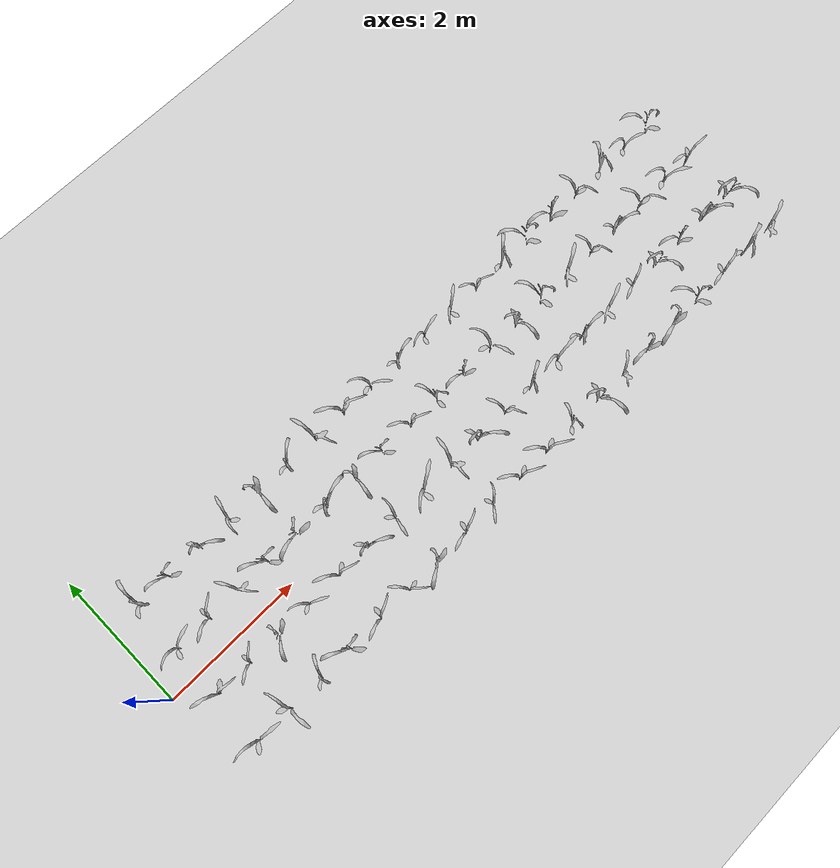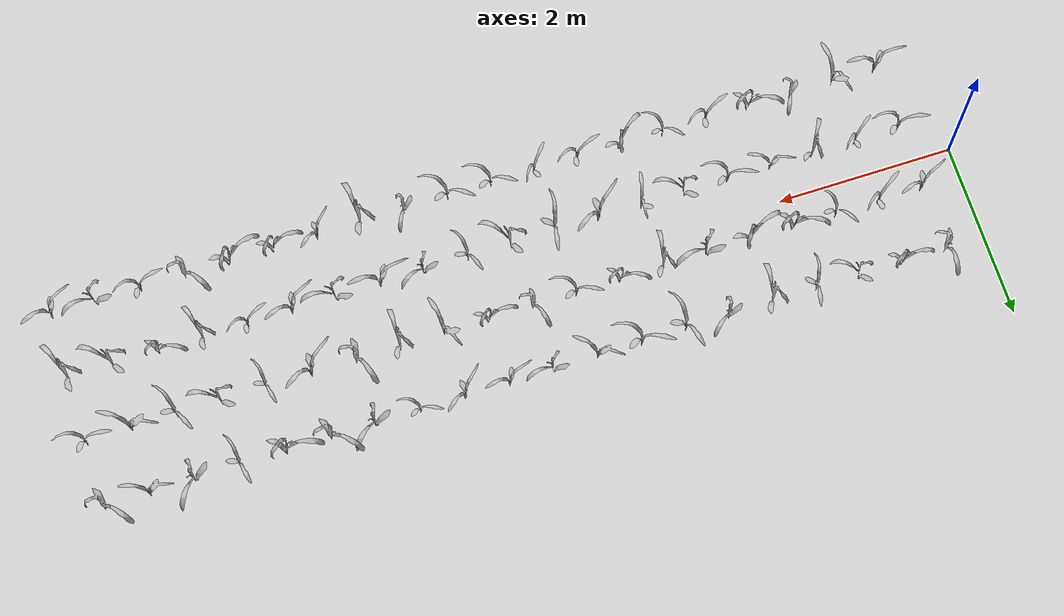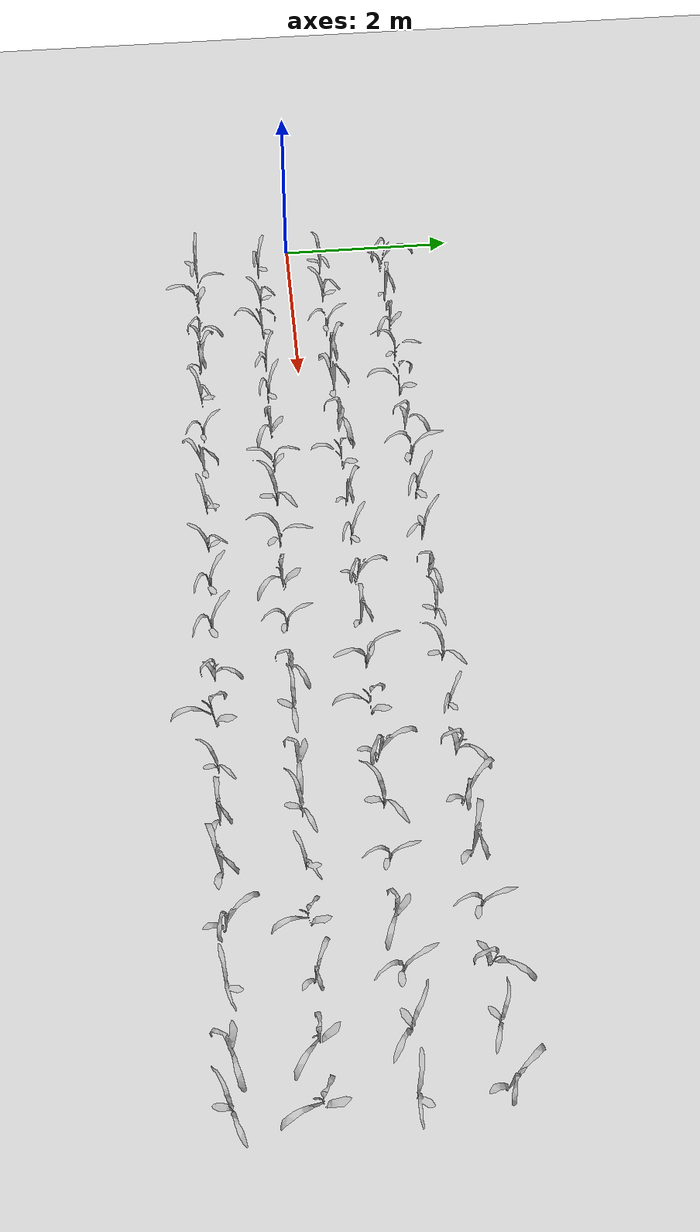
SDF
<sdf version="1.6">
 <world name="default">
  <light name="sun" type="directional">
   <pose>0 0 10 0 -0 0</pose>
   <diffuse>0.8 0.8 0.8 1</diffuse>
   <specular>0.2 0.2 0.2 1</specular>
   <attenuation>
    <range>1000</range>
    <constant>0.9</constant>
    <linear>0.01</linear>
    <quadratic>0.001</quadratic>
   </attenuation>
   <direction>-0.5 0.1 -0.9</direction>
  </light>
  <model name="ground_plane">
   <static>1</static>
   <link name="link">
    <collision name="collision">
     <geometry><plane><normal>0 0 1</normal><size>100 100</size></plane></geometry>
     <surface>
      <contact><collide_bitmask>65535</collide_bitmask></contact>
      <friction><ode><mu>100</mu><mu2>50</mu2></ode></friction>
     </surface>
    </collision>
    <visual name="visual">
     <cast_shadows>0</cast_shadows>
     <geometry><plane><normal>0 0 1</normal><size>100 100</size></plane></geometry>
     <material>
      <script><uri>file://media/materials/scripts/gazebo.material</uri><name>Gazebo/Grey</name></script>
     </material>
    </visual>
   </link>
  </model>
  <gravity>0 0 -9.8</gravity>
  <magnetic_field>6e-06 2.3e-05 -4.2e-05</magnetic_field>
  <atmosphere type="adiabatic"/>
  <physics name="default_physics" default="0" type="ode">
   <max_step_size>0.001</max_step_size>
   <real_time_factor>1</real_time_factor>
   <real_time_update_rate>1000</real_time_update_rate>
  </physics>
  <scene><ambient>0.4 0.4 0.4 1</ambient><background>0.7 0.7 0.7 1</background><shadows>1</shadows></scene>
  <audio><device>default</device></audio>
  <spherical_coordinates>
   <surface_model>EARTH_WGS84</surface_model>
   <latitude_deg>0</latitude_deg>
   <longitude_deg>0</longitude_deg>
   <elevation>0</elevation>
   <heading_deg>0</heading_deg>
  </spherical_coordinates>
  <model name="maize_02_0000">
   <pose>0.5 0.375 0.05 0 -0 2.486436329962448</pose>
   <link name="maize_02_0000_link">
    <inertial>
     <mass>5.0</mass>
     <inertia>
      <ixx>0.0033416667</ixx>
      <ixy>0</ixy>
      <ixz>0</ixz>
      <iyy>0.0033416667</iyy>
      <iyz>0</iyz>
      <izz>0.000016666667</izz>
     </inertia>
     <pose>0 0 0.1 0 0 0</pose>
    </inertial>
    <collision name="collision">
     <pose>0 0 0.2 0 -0 0</pose>
     <geometry><box><size>0.02 0.02 0.4</size></box></geometry>
     <surface><friction><ode><mu>10</mu><mu2>10</mu2></ode></friction></surface>
    </collision>
    <visual name="visual">
     <geometry>
      <mesh>
       <uri>model://maize_02/meshes/maize_02.dae</uri>
       <scale>0.594464190907645 0.594464190907645 0.594464190907645</scale>
      </mesh>
     </geometry>
    </visual>
   </link>
  </model>
  <model name="maize_01_0001">
   <pose>0.5 1.125 0.05 0 -0 2.298788414996738</pose>
   <link name="maize_01_0001_link">
    <inertial>
     <mass>5.0</mass>
     <inertia>
      <ixx>0.0033416667</ixx>
      <ixy>0</ixy>
      <ixz>0</ixz>
      <iyy>0.0033416667</iyy>
      <iyz>0</iyz>
      <izz>0.000016666667</izz>
     </inertia>
     <pose>0 0 0.1 0 0 0</pose>
    </inertial>
    <collision name="collision">
     <pose>0 0 0.2 0 -0 0</pose>
     <geometry><box><size>0.02 0.02 0.4</size></box></geometry>
     <surface><friction><ode><mu>10</mu><mu2>10</mu2></ode></friction></surface>
    </collision>
    <visual name="visual">
     <geometry>
      <mesh>
       <uri>model://maize_01/meshes/maize_01.dae</uri>
       <scale>0.6277734751738697 0.6277734751738697 0.6277734751738697</scale>
      </mesh>
     </geometry>
    </visual>
   </link>
  </model>
  <model name="maize_02_0002">
   <pose>0.5 -0.375 0.05 0 -0 5.080375280023383</pose>
   <link name="maize_02_0002_link">
    <inertial>
     <mass>5.0</mass>
     <inertia>
      <ixx>0.0033416667</ixx>
      <ixy>0</ixy>
      <ixz>0</ixz>
      <iyy>0.0033416667</iyy>
      <iyz>0</iyz>
      <izz>0.000016666667</izz>
     </inertia>
     <pose>0 0 0.1 0 0 0</pose>
    </inertial>
    <collision name="collision">
     <pose>0 0 0.2 0 -0 0</pose>
     <geometry><box><size>0.02 0.02 0.4</size></box></geometry>
     <surface><friction><ode><mu>10</mu><mu2>10</mu2></ode></friction></surface>
    </collision>
    <visual name="visual">
     <geometry>
      <mesh>
       <uri>model://maize_02/meshes/maize_02.dae</uri>
       <scale>0.6373901294734036 0.6373901294734036 0.6373901294734036</scale>
      </mesh>
     </geometry>
    </visual>
   </link>
  </model>
  <model name="maize_02_0003">
   <pose>0.5 -1.125 0.05 0 -0 2.0655652335273587</pose>
   <link name="maize_02_0003_link">
    <inertial>
     <mass>5.0</mass>
     <inertia>
      <ixx>0.0033416667</ixx>
      <ixy>0</ixy>
      <ixz>0</ixz>
      <iyy>0.0033416667</iyy>
      <iyz>0</iyz>
      <izz>0.000016666667</izz>
     </inertia>
     <pose>0 0 0.1 0 0 0</pose>
    </inertial>
    <collision name="collision">
     <pose>0 0 0.2 0 -0 0</pose>
     <geometry><box><size>0.02 0.02 0.4</size></box></geometry>
     <surface><friction><ode><mu>10</mu><mu2>10</mu2></ode></friction></surface>
    </collision>
    <visual name="visual">
     <geometry>
      <mesh>
       <uri>model://maize_02/meshes/maize_02.dae</uri>
       <scale>0.6587457137448713 0.6587457137448713 0.6587457137448713</scale>
      </mesh>
     </geometry>
    </visual>
   </link>
  </model>
  <model name="maize_02_0004">
   <pose>1.0 0.375 0.05 0 -0 5.888778220820629</pose>
   <link name="maize_02_0004_link">
    <inertial>
     <mass>5.0</mass>
     <inertia>
      <ixx>0.0033416667</ixx>
      <ixy>0</ixy>
      <ixz>0</ixz>
      <iyy>0.0033416667</iyy>
      <iyz>0</iyz>
      <izz>0.000016666667</izz>
     </inertia>
     <pose>0 0 0.1 0 0 0</pose>
    </inertial>
    <collision name="collision">
     <pose>0 0 0.2 0 -0 0</pose>
     <geometry><box><size>0.02 0.02 0.4</size></box></geometry>
     <surface><friction><ode><mu>10</mu><mu2>10</mu2></ode></friction></surface>
    </collision>
    <visual name="visual">
     <geometry>
      <mesh>
       <uri>model://maize_02/meshes/maize_02.dae</uri>
       <scale>0.5925092554410509 0.5925092554410509 0.5925092554410509</scale>
      </mesh>
     </geometry>
    </visual>
   </link>
  </model>
  <model name="maize_01_0005">
   <pose>1.0 1.125 0.05 0 -0 3.800942496032068</pose>
   <link name="maize_01_0005_link">
    <inertial>
     <mass>5.0</mass>
     <inertia>
      <ixx>0.0033416667</ixx>
      <ixy>0</ixy>
      <ixz>0</ixz>
      <iyy>0.0033416667</iyy>
      <iyz>0</iyz>
      <izz>0.000016666667</izz>
     </inertia>
     <pose>0 0 0.1 0 0 0</pose>
    </inertial>
    <collision name="collision">
     <pose>0 0 0.2 0 -0 0</pose>
     <geometry><box><size>0.02 0.02 0.4</size></box></geometry>
     <surface><friction><ode><mu>10</mu><mu2>10</mu2></ode></friction></surface>
    </collision>
    <visual name="visual">
     <geometry>
      <mesh>
       <uri>model://maize_01/meshes/maize_01.dae</uri>
       <scale>0.5658001392971347 0.5658001392971347 0.5658001392971347</scale>
      </mesh>
     </geometry>
    </visual>
   </link>
  </model>
  <model name="maize_02_0006">
   <pose>1.0 -0.375 0.05 0 -0 5.960453748156834</pose>
   <link name="maize_02_0006_link">
    <inertial>
     <mass>5.0</mass>
     <inertia>
      <ixx>0.0033416667</ixx>
      <ixy>0</ixy>
      <ixz>0</ixz>
      <iyy>0.0033416667</iyy>
      <iyz>0</iyz>
      <izz>0.000016666667</izz>
     </inertia>
     <pose>0 0 0.1 0 0 0</pose>
    </inertial>
    <collision name="collision">
     <pose>0 0 0.2 0 -0 0</pose>
     <geometry><box><size>0.02 0.02 0.4</size></box></geometry>
     <surface><friction><ode><mu>10</mu><mu2>10</mu2></ode></friction></surface>
    </collision>
    <visual name="visual">
     <geometry>
      <mesh>
       <uri>model://maize_02/meshes/maize_02.dae</uri>
       <scale>0.5101669844444433 0.5101669844444433 0.5101669844444433</scale>
      </mesh>
     </geometry>
    </visual>
   </link>
  </model>
  <model name="maize_02_0007">
   <pose>1.0 -1.125 0.05 0 -0 0.7257184616854857</pose>
   <link name="maize_02_0007_link">
    <inertial>
     <mass>5.0</mass>
     <inertia>
      <ixx>0.0033416667</ixx>
      <ixy>0</ixy>
      <ixz>0</ixz>
      <iyy>0.0033416667</iyy>
      <iyz>0</iyz>
      <izz>0.000016666667</izz>
     </inertia>
     <pose>0 0 0.1 0 0 0</pose>
    </inertial>
    <collision name="collision">
     <pose>0 0 0.2 0 -0 0</pose>
     <geometry><box><size>0.02 0.02 0.4</size></box></geometry>
     <surface><friction><ode><mu>10</mu><mu2>10</mu2></ode></friction></surface>
    </collision>
    <visual name="visual">
     <geometry>
      <mesh>
       <uri>model://maize_02/meshes/maize_02.dae</uri>
       <scale>0.6774858792550148 0.6774858792550148 0.6774858792550148</scale>
      </mesh>
     </geometry>
    </visual>
   </link>
  </model>
  <model name="maize_02_0008">
   <pose>1.5 0.375 0.05 0 -0 4.276486220324584</pose>
   <link name="maize_02_0008_link">
    <inertial>
     <mass>5.0</mass>
     <inertia>
      <ixx>0.0033416667</ixx>
      <ixy>0</ixy>
      <ixz>0</ixz>
      <iyy>0.0033416667</iyy>
      <iyz>0</iyz>
      <izz>0.000016666667</izz>
     </inertia>
     <pose>0 0 0.1 0 0 0</pose>
    </inertial>
    <collision name="collision">
     <pose>0 0 0.2 0 -0 0</pose>
     <geometry><box><size>0.02 0.02 0.4</size></box></geometry>
     <surface><friction><ode><mu>10</mu><mu2>10</mu2></ode></friction></surface>
    </collision>
    <visual name="visual">
     <geometry>
      <mesh>
       <uri>model://maize_02/meshes/maize_02.dae</uri>
       <scale>0.5624697977309072 0.5624697977309072 0.5624697977309072</scale>
      </mesh>
     </geometry>
    </visual>
   </link>
  </model>
  <model name="maize_01_0009">
   <pose>1.5 1.125 0.05 0 -0 0.226990537836368</pose>
   <link name="maize_01_0009_link">
    <inertial>
     <mass>5.0</mass>
     <inertia>
      <ixx>0.0033416667</ixx>
      <ixy>0</ixy>
      <ixz>0</ixz>
      <iyy>0.0033416667</iyy>
      <iyz>0</iyz>
      <izz>0.000016666667</izz>
     </inertia>
     <pose>0 0 0.1 0 0 0</pose>
    </inertial>
    <collision name="collision">
     <pose>0 0 0.2 0 -0 0</pose>
     <geometry><box><size>0.02 0.02 0.4</size></box></geometry>
     <surface><friction><ode><mu>10</mu><mu2>10</mu2></ode></friction></surface>
    </collision>
    <visual name="visual">
     <geometry>
      <mesh>
       <uri>model://maize_01/meshes/maize_01.dae</uri>
       <scale>0.5509734204890646 0.5509734204890646 0.5509734204890646</scale>
      </mesh>
     </geometry>
    </visual>
   </link>
  </model>
  <model name="maize_01_0010">
   <pose>1.5 -0.375 0.05 0 -0 4.998152133039663</pose>
   <link name="maize_01_0010_link">
    <inertial>
     <mass>5.0</mass>
     <inertia>
      <ixx>0.0033416667</ixx>
      <ixy>0</ixy>
      <ixz>0</ixz>
      <iyy>0.0033416667</iyy>
      <iyz>0</iyz>
      <izz>0.000016666667</izz>
     </inertia>
     <pose>0 0 0.1 0 0 0</pose>
    </inertial>
    <collision name="collision">
     <pose>0 0 0.2 0 -0 0</pose>
     <geometry><box><size>0.02 0.02 0.4</size></box></geometry>
     <surface><friction><ode><mu>10</mu><mu2>10</mu2></ode></friction></surface>
    </collision>
    <visual name="visual">
     <geometry>
      <mesh>
       <uri>model://maize_01/meshes/maize_01.dae</uri>
       <scale>0.5865168241783152 0.5865168241783152 0.5865168241783152</scale>
      </mesh>
     </geometry>
    </visual>
   </link>
  </model>
  <model name="maize_01_0011">
   <pose>1.5 -1.125 0.05 0 -0 1.9324223692315545</pose>
   <link name="maize_01_0011_link">
    <inertial>
     <mass>5.0</mass>
     <inertia>
      <ixx>0.0033416667</ixx>
      <ixy>0</ixy>
      <ixz>0</ixz>
      <iyy>0.0033416667</iyy>
      <iyz>0</iyz>
      <izz>0.000016666667</izz>
     </inertia>
     <pose>0 0 0.1 0 0 0</pose>
    </inertial>
    <collision name="collision">
     <pose>0 0 0.2 0 -0 0</pose>
     <geometry><box><size>0.02 0.02 0.4</size></box></geometry>
     <surface><friction><ode><mu>10</mu><mu2>10</mu2></ode></friction></surface>
    </collision>
    <visual name="visual">
     <geometry>
      <mesh>
       <uri>model://maize_01/meshes/maize_01.dae</uri>
       <scale>0.5003540891792582 0.5003540891792582 0.5003540891792582</scale>
      </mesh>
     </geometry>
    </visual>
   </link>
  </model>
  <model name="maize_01_0012">
   <pose>2.0 0.375 0.05 0 -0 3.506546388485013</pose>
   <link name="maize_01_0012_link">
    <inertial>
     <mass>5.0</mass>
     <inertia>
      <ixx>0.0033416667</ixx>
      <ixy>0</ixy>
      <ixz>0</ixz>
      <iyy>0.0033416667</iyy>
      <iyz>0</iyz>
      <izz>0.000016666667</izz>
     </inertia>
     <pose>0 0 0.1 0 0 0</pose>
    </inertial>
    <collision name="collision">
     <pose>0 0 0.2 0 -0 0</pose>
     <geometry><box><size>0.02 0.02 0.4</size></box></geometry>
     <surface><friction><ode><mu>10</mu><mu2>10</mu2></ode></friction></surface>
    </collision>
    <visual name="visual">
     <geometry>
      <mesh>
       <uri>model://maize_01/meshes/maize_01.dae</uri>
       <scale>0.6499434881953365 0.6499434881953365 0.6499434881953365</scale>
      </mesh>
     </geometry>
    </visual>
   </link>
  </model>
  <model name="maize_02_0013">
   <pose>2.0 1.125 0.05 0 -0 3.5083101263330416</pose>
   <link name="maize_02_0013_link">
    <inertial>
     <mass>5.0</mass>
     <inertia>
      <ixx>0.0033416667</ixx>
      <ixy>0</ixy>
      <ixz>0</ixz>
      <iyy>0.0033416667</iyy>
      <iyz>0</iyz>
      <izz>0.000016666667</izz>
     </inertia>
     <pose>0 0 0.1 0 0 0</pose>
    </inertial>
    <collision name="collision">
     <pose>0 0 0.2 0 -0 0</pose>
     <geometry><box><size>0.02 0.02 0.4</size></box></geometry>
     <surface><friction><ode><mu>10</mu><mu2>10</mu2></ode></friction></surface>
    </collision>
    <visual name="visual">
     <geometry>
      <mesh>
       <uri>model://maize_02/meshes/maize_02.dae</uri>
       <scale>0.5802755091073676 0.5802755091073676 0.5802755091073676</scale>
      </mesh>
     </geometry>
    </visual>
   </link>
  </model>
  <model name="maize_02_0014">
   <pose>2.0 -0.375 0.05 0 -0 1.6967970722052805</pose>
   <link name="maize_02_0014_link">
    <inertial>
     <mass>5.0</mass>
     <inertia>
      <ixx>0.0033416667</ixx>
      <ixy>0</ixy>
      <ixz>0</ixz>
      <iyy>0.0033416667</iyy>
      <iyz>0</iyz>
      <izz>0.000016666667</izz>
     </inertia>
     <pose>0 0 0.1 0 0 0</pose>
    </inertial>
    <collision name="collision">
     <pose>0 0 0.2 0 -0 0</pose>
     <geometry><box><size>0.02 0.02 0.4</size></box></geometry>
     <surface><friction><ode><mu>10</mu><mu2>10</mu2></ode></friction></surface>
    </collision>
    <visual name="visual">
     <geometry>
      <mesh>
       <uri>model://maize_02/meshes/maize_02.dae</uri>
       <scale>0.5231342005749441 0.5231342005749441 0.5231342005749441</scale>
      </mesh>
     </geometry>
    </visual>
   </link>
  </model>
  <model name="maize_01_0015">
   <pose>2.0 -1.125 0.05 0 -0 3.519975309279825</pose>
   <link name="maize_01_0015_link">
    <inertial>
     <mass>5.0</mass>
     <inertia>
      <ixx>0.0033416667</ixx>
      <ixy>0</ixy>
      <ixz>0</ixz>
      <iyy>0.0033416667</iyy>
      <iyz>0</iyz>
      <izz>0.000016666667</izz>
     </inertia>
     <pose>0 0 0.1 0 0 0</pose>
    </inertial>
    <collision name="collision">
     <pose>0 0 0.2 0 -0 0</pose>
     <geometry><box><size>0.02 0.02 0.4</size></box></geometry>
     <surface><friction><ode><mu>10</mu><mu2>10</mu2></ode></friction></surface>
    </collision>
    <visual name="visual">
     <geometry>
      <mesh>
       <uri>model://maize_01/meshes/maize_01.dae</uri>
       <scale>0.6468035016286179 0.6468035016286179 0.6468035016286179</scale>
      </mesh>
     </geometry>
    </visual>
   </link>
  </model>
  <model name="maize_01_0016">
   <pose>2.5 0.375 0.05 0 -0 4.247404974419108</pose>
   <link name="maize_01_0016_link">
    <inertial>
     <mass>5.0</mass>
     <inertia>
      <ixx>0.0033416667</ixx>
      <ixy>0</ixy>
      <ixz>0</ixz>
      <iyy>0.0033416667</iyy>
      <iyz>0</iyz>
      <izz>0.000016666667</izz>
     </inertia>
     <pose>0 0 0.1 0 0 0</pose>
    </inertial>
    <collision name="collision">
     <pose>0 0 0.2 0 -0 0</pose>
     <geometry><box><size>0.02 0.02 0.4</size></box></geometry>
     <surface><friction><ode><mu>10</mu><mu2>10</mu2></ode></friction></surface>
    </collision>
    <visual name="visual">
     <geometry>
      <mesh>
       <uri>model://maize_01/meshes/maize_01.dae</uri>
       <scale>0.6690471731804969 0.6690471731804969 0.6690471731804969</scale>
      </mesh>
     </geometry>
    </visual>
   </link>
  </model>
  <model name="maize_01_0017">
   <pose>2.5 1.125 0.05 0 -0 5.449269828116384</pose>
   <link name="maize_01_0017_link">
    <inertial>
     <mass>5.0</mass>
     <inertia>
      <ixx>0.0033416667</ixx>
      <ixy>0</ixy>
      <ixz>0</ixz>
      <iyy>0.0033416667</iyy>
      <iyz>0</iyz>
      <izz>0.000016666667</izz>
     </inertia>
     <pose>0 0 0.1 0 0 0</pose>
    </inertial>
    <collision name="collision">
     <pose>0 0 0.2 0 -0 0</pose>
     <geometry><box><size>0.02 0.02 0.4</size></box></geometry>
     <surface><friction><ode><mu>10</mu><mu2>10</mu2></ode></friction></surface>
    </collision>
    <visual name="visual">
     <geometry>
      <mesh>
       <uri>model://maize_01/meshes/maize_01.dae</uri>
       <scale>0.6421622239480822 0.6421622239480822 0.6421622239480822</scale>
      </mesh>
     </geometry>
    </visual>
   </link>
  </model>
  <model name="maize_02_0018">
   <pose>2.5 -0.375 0.05 0 -0 4.906010909218893</pose>
   <link name="maize_02_0018_link">
    <inertial>
     <mass>5.0</mass>
     <inertia>
      <ixx>0.0033416667</ixx>
      <ixy>0</ixy>
      <ixz>0</ixz>
      <iyy>0.0033416667</iyy>
      <iyz>0</iyz>
      <izz>0.000016666667</izz>
     </inertia>
     <pose>0 0 0.1 0 0 0</pose>
    </inertial>
    <collision name="collision">
     <pose>0 0 0.2 0 -0 0</pose>
     <geometry><box><size>0.02 0.02 0.4</size></box></geometry>
     <surface><friction><ode><mu>10</mu><mu2>10</mu2></ode></friction></surface>
    </collision>
    <visual name="visual">
     <geometry>
      <mesh>
       <uri>model://maize_02/meshes/maize_02.dae</uri>
       <scale>0.626600553921358 0.626600553921358 0.626600553921358</scale>
      </mesh>
     </geometry>
    </visual>
   </link>
  </model>
  <model name="maize_02_0019">
   <pose>2.5 -1.125 0.05 0 -0 5.69318676119266</pose>
   <link name="maize_02_0019_link">
    <inertial>
     <mass>5.0</mass>
     <inertia>
      <ixx>0.0033416667</ixx>
      <ixy>0</ixy>
      <ixz>0</ixz>
      <iyy>0.0033416667</iyy>
      <iyz>0</iyz>
      <izz>0.000016666667</izz>
     </inertia>
     <pose>0 0 0.1 0 0 0</pose>
    </inertial>
    <collision name="collision">
     <pose>0 0 0.2 0 -0 0</pose>
     <geometry><box><size>0.02 0.02 0.4</size></box></geometry>
     <surface><friction><ode><mu>10</mu><mu2>10</mu2></ode></friction></surface>
    </collision>
    <visual name="visual">
     <geometry>
      <mesh>
       <uri>model://maize_02/meshes/maize_02.dae</uri>
       <scale>0.5929270849490827 0.5929270849490827 0.5929270849490827</scale>
      </mesh>
     </geometry>
    </visual>
   </link>
  </model>
  <model name="maize_01_0020">
   <pose>3.0 0.375 0.05 0 -0 1.043117871051002</pose>
   <link name="maize_01_0020_link">
    <inertial>
     <mass>5.0</mass>
     <inertia>
      <ixx>0.0033416667</ixx>
      <ixy>0</ixy>
      <ixz>0</ixz>
      <iyy>0.0033416667</iyy>
      <iyz>0</iyz>
      <izz>0.000016666667</izz>
     </inertia>
     <pose>0 0 0.1 0 0 0</pose>
    </inertial>
    <collision name="collision">
     <pose>0 0 0.2 0 -0 0</pose>
     <geometry><box><size>0.02 0.02 0.4</size></box></geometry>
     <surface><friction><ode><mu>10</mu><mu2>10</mu2></ode></friction></surface>
    </collision>
    <visual name="visual">
     <geometry>
      <mesh>
       <uri>model://maize_01/meshes/maize_01.dae</uri>
       <scale>0.6769761855756116 0.6769761855756116 0.6769761855756116</scale>
      </mesh>
     </geometry>
    </visual>
   </link>
  </model>
  <model name="maize_01_0021">
   <pose>3.0 1.125 0.05 0 -0 1.5060979926703266</pose>
   <link name="maize_01_0021_link">
    <inertial>
     <mass>5.0</mass>
     <inertia>
      <ixx>0.0033416667</ixx>
      <ixy>0</ixy>
      <ixz>0</ixz>
      <iyy>0.0033416667</iyy>
      <iyz>0</iyz>
      <izz>0.000016666667</izz>
     </inertia>
     <pose>0 0 0.1 0 0 0</pose>
    </inertial>
    <collision name="collision">
     <pose>0 0 0.2 0 -0 0</pose>
     <geometry><box><size>0.02 0.02 0.4</size></box></geometry>
     <surface><friction><ode><mu>10</mu><mu2>10</mu2></ode></friction></surface>
    </collision>
    <visual name="visual">
     <geometry>
      <mesh>
       <uri>model://maize_01/meshes/maize_01.dae</uri>
       <scale>0.5539245820906094 0.5539245820906094 0.5539245820906094</scale>
      </mesh>
     </geometry>
    </visual>
   </link>
  </model>
  <model name="maize_01_0022">
   <pose>3.0 -0.375 0.05 0 -0 0.33031992653440345</pose>
   <link name="maize_01_0022_link">
    <inertial>
     <mass>5.0</mass>
     <inertia>
      <ixx>0.0033416667</ixx>
      <ixy>0</ixy>
      <ixz>0</ixz>
      <iyy>0.0033416667</iyy>
      <iyz>0</iyz>
      <izz>0.000016666667</izz>
     </inertia>
     <pose>0 0 0.1 0 0 0</pose>
    </inertial>
    <collision name="collision">
     <pose>0 0 0.2 0 -0 0</pose>
     <geometry><box><size>0.02 0.02 0.4</size></box></geometry>
     <surface><friction><ode><mu>10</mu><mu2>10</mu2></ode></friction></surface>
    </collision>
    <visual name="visual">
     <geometry>
      <mesh>
       <uri>model://maize_01/meshes/maize_01.dae</uri>
       <scale>0.5847663939026114 0.5847663939026114 0.5847663939026114</scale>
      </mesh>
     </geometry>
    </visual>
   </link>
  </model>
  <model name="maize_02_0023">
   <pose>3.0 -1.125 0.05 0 -0 4.489898993022544</pose>
   <link name="maize_02_0023_link">
    <inertial>
     <mass>5.0</mass>
     <inertia>
      <ixx>0.0033416667</ixx>
      <ixy>0</ixy>
      <ixz>0</ixz>
      <iyy>0.0033416667</iyy>
      <iyz>0</iyz>
      <izz>0.000016666667</izz>
     </inertia>
     <pose>0 0 0.1 0 0 0</pose>
    </inertial>
    <collision name="collision">
     <pose>0 0 0.2 0 -0 0</pose>
     <geometry><box><size>0.02 0.02 0.4</size></box></geometry>
     <surface><friction><ode><mu>10</mu><mu2>10</mu2></ode></friction></surface>
    </collision>
    <visual name="visual">
     <geometry>
      <mesh>
       <uri>model://maize_02/meshes/maize_02.dae</uri>
       <scale>0.5223654487258567 0.5223654487258567 0.5223654487258567</scale>
      </mesh>
     </geometry>
    </visual>
   </link>
  </model>
  <model name="maize_01_0024">
   <pose>3.5 0.375 0.05 0 -0 5.3651282673576715</pose>
   <link name="maize_01_0024_link">
    <inertial>
     <mass>5.0</mass>
     <inertia>
      <ixx>0.0033416667</ixx>
      <ixy>0</ixy>
      <ixz>0</ixz>
      <iyy>0.0033416667</iyy>
      <iyz>0</iyz>
      <izz>0.000016666667</izz>
     </inertia>
     <pose>0 0 0.1 0 0 0</pose>
    </inertial>
    <collision name="collision">
     <pose>0 0 0.2 0 -0 0</pose>
     <geometry><box><size>0.02 0.02 0.4</size></box></geometry>
     <surface><friction><ode><mu>10</mu><mu2>10</mu2></ode></friction></surface>
    </collision>
    <visual name="visual">
     <geometry>
      <mesh>
       <uri>model://maize_01/meshes/maize_01.dae</uri>
       <scale>0.5986903436208948 0.5986903436208948 0.5986903436208948</scale>
      </mesh>
     </geometry>
    </visual>
   </link>
  </model>
  <model name="maize_02_0025">
   <pose>3.5 1.125 0.05 0 -0 3.974233096109407</pose>
   <link name="maize_02_0025_link">
    <inertial>
     <mass>5.0</mass>
     <inertia>
      <ixx>0.0033416667</ixx>
      <ixy>0</ixy>
      <ixz>0</ixz>
      <iyy>0.0033416667</iyy>
      <iyz>0</iyz>
      <izz>0.000016666667</izz>
     </inertia>
     <pose>0 0 0.1 0 0 0</pose>
    </inertial>
    <collision name="collision">
     <pose>0 0 0.2 0 -0 0</pose>
     <geometry><box><size>0.02 0.02 0.4</size></box></geometry>
     <surface><friction><ode><mu>10</mu><mu2>10</mu2></ode></friction></surface>
    </collision>
    <visual name="visual">
     <geometry>
      <mesh>
       <uri>model://maize_02/meshes/maize_02.dae</uri>
       <scale>0.6840697809252837 0.6840697809252837 0.6840697809252837</scale>
      </mesh>
     </geometry>
    </visual>
   </link>
  </model>
  <model name="maize_02_0026">
   <pose>3.5 -0.375 0.05 0 -0 0.3855338366262953</pose>
   <link name="maize_02_0026_link">
    <inertial>
     <mass>5.0</mass>
     <inertia>
      <ixx>0.0033416667</ixx>
      <ixy>0</ixy>
      <ixz>0</ixz>
      <iyy>0.0033416667</iyy>
      <iyz>0</iyz>
      <izz>0.000016666667</izz>
     </inertia>
     <pose>0 0 0.1 0 0 0</pose>
    </inertial>
    <collision name="collision">
     <pose>0 0 0.2 0 -0 0</pose>
     <geometry><box><size>0.02 0.02 0.4</size></box></geometry>
     <surface><friction><ode><mu>10</mu><mu2>10</mu2></ode></friction></surface>
    </collision>
    <visual name="visual">
     <geometry>
      <mesh>
       <uri>model://maize_02/meshes/maize_02.dae</uri>
       <scale>0.5689283618021689 0.5689283618021689 0.5689283618021689</scale>
      </mesh>
     </geometry>
    </visual>
   </link>
  </model>
  <model name="maize_01_0027">
   <pose>3.5 -1.125 0.05 0 -0 4.535984097456068</pose>
   <link name="maize_01_0027_link">
    <inertial>
     <mass>5.0</mass>
     <inertia>
      <ixx>0.0033416667</ixx>
      <ixy>0</ixy>
      <ixz>0</ixz>
      <iyy>0.0033416667</iyy>
      <iyz>0</iyz>
      <izz>0.000016666667</izz>
     </inertia>
     <pose>0 0 0.1 0 0 0</pose>
    </inertial>
    <collision name="collision">
     <pose>0 0 0.2 0 -0 0</pose>
     <geometry><box><size>0.02 0.02 0.4</size></box></geometry>
     <surface><friction><ode><mu>10</mu><mu2>10</mu2></ode></friction></surface>
    </collision>
    <visual name="visual">
     <geometry>
      <mesh>
       <uri>model://maize_01/meshes/maize_01.dae</uri>
       <scale>0.6088326556180363 0.6088326556180363 0.6088326556180363</scale>
      </mesh>
     </geometry>
    </visual>
   </link>
  </model>
  <model name="maize_01_0028">
   <pose>4.0 0.375 0.05 0 -0 3.485553312830647</pose>
   <link name="maize_01_0028_link">
    <inertial>
     <mass>5.0</mass>
     <inertia>
      <ixx>0.0033416667</ixx>
      <ixy>0</ixy>
      <ixz>0</ixz>
      <iyy>0.0033416667</iyy>
      <iyz>0</iyz>
      <izz>0.000016666667</izz>
     </inertia>
     <pose>0 0 0.1 0 0 0</pose>
    </inertial>
    <collision name="collision">
     <pose>0 0 0.2 0 -0 0</pose>
     <geometry><box><size>0.02 0.02 0.4</size></box></geometry>
     <surface><friction><ode><mu>10</mu><mu2>10</mu2></ode></friction></surface>
    </collision>
    <visual name="visual">
     <geometry>
      <mesh>
       <uri>model://maize_01/meshes/maize_01.dae</uri>
       <scale>0.5595020058112883 0.5595020058112883 0.5595020058112883</scale>
      </mesh>
     </geometry>
    </visual>
   </link>
  </model>
  <model name="maize_02_0029">
   <pose>4.0 1.125 0.05 0 -0 4.791513384607671</pose>
   <link name="maize_02_0029_link">
    <inertial>
     <mass>5.0</mass>
     <inertia>
      <ixx>0.0033416667</ixx>
      <ixy>0</ixy>
      <ixz>0</ixz>
      <iyy>0.0033416667</iyy>
      <iyz>0</iyz>
      <izz>0.000016666667</izz>
     </inertia>
     <pose>0 0 0.1 0 0 0</pose>
    </inertial>
    <collision name="collision">
     <pose>0 0 0.2 0 -0 0</pose>
     <geometry><box><size>0.02 0.02 0.4</size></box></geometry>
     <surface><friction><ode><mu>10</mu><mu2>10</mu2></ode></friction></surface>
    </collision>
    <visual name="visual">
     <geometry>
      <mesh>
       <uri>model://maize_02/meshes/maize_02.dae</uri>
       <scale>0.6988486792723937 0.6988486792723937 0.6988486792723937</scale>
      </mesh>
     </geometry>
    </visual>
   </link>
  </model>
  <model name="maize_02_0030">
   <pose>4.0 -0.375 0.05 0 -0 2.7621582964979345</pose>
   <link name="maize_02_0030_link">
    <inertial>
     <mass>5.0</mass>
     <inertia>
      <ixx>0.0033416667</ixx>
      <ixy>0</ixy>
      <ixz>0</ixz>
      <iyy>0.0033416667</iyy>
      <iyz>0</iyz>
      <izz>0.000016666667</izz>
     </inertia>
     <pose>0 0 0.1 0 0 0</pose>
    </inertial>
    <collision name="collision">
     <pose>0 0 0.2 0 -0 0</pose>
     <geometry><box><size>0.02 0.02 0.4</size></box></geometry>
     <surface><friction><ode><mu>10</mu><mu2>10</mu2></ode></friction></surface>
    </collision>
    <visual name="visual">
     <geometry>
      <mesh>
       <uri>model://maize_02/meshes/maize_02.dae</uri>
       <scale>0.6989581909866358 0.6989581909866358 0.6989581909866358</scale>
      </mesh>
     </geometry>
    </visual>
   </link>
  </model>
  <model name="maize_02_0031">
   <pose>4.0 -1.125 0.05 0 -0 5.6240680111964645</pose>
   <link name="maize_02_0031_link">
    <inertial>
     <mass>5.0</mass>
     <inertia>
      <ixx>0.0033416667</ixx>
      <ixy>0</ixy>
      <ixz>0</ixz>
      <iyy>0.0033416667</iyy>
      <iyz>0</iyz>
      <izz>0.000016666667</izz>
     </inertia>
     <pose>0 0 0.1 0 0 0</pose>
    </inertial>
    <collision name="collision">
     <pose>0 0 0.2 0 -0 0</pose>
     <geometry><box><size>0.02 0.02 0.4</size></box></geometry>
     <surface><friction><ode><mu>10</mu><mu2>10</mu2></ode></friction></surface>
    </collision>
    <visual name="visual">
     <geometry>
      <mesh>
       <uri>model://maize_02/meshes/maize_02.dae</uri>
       <scale>0.5756476119257931 0.5756476119257931 0.5756476119257931</scale>
      </mesh>
     </geometry>
    </visual>
   </link>
  </model>
  <model name="maize_02_0032">
   <pose>4.5 0.375 0.05 0 -0 4.8015691944950385</pose>
   <link name="maize_02_0032_link">
    <inertial>
     <mass>5.0</mass>
     <inertia>
      <ixx>0.0033416667</ixx>
      <ixy>0</ixy>
      <ixz>0</ixz>
      <iyy>0.0033416667</iyy>
      <iyz>0</iyz>
      <izz>0.000016666667</izz>
     </inertia>
     <pose>0 0 0.1 0 0 0</pose>
    </inertial>
    <collision name="collision">
     <pose>0 0 0.2 0 -0 0</pose>
     <geometry><box><size>0.02 0.02 0.4</size></box></geometry>
     <surface><friction><ode><mu>10</mu><mu2>10</mu2></ode></friction></surface>
    </collision>
    <visual name="visual">
     <geometry>
      <mesh>
       <uri>model://maize_02/meshes/maize_02.dae</uri>
       <scale>0.5925649161468299 0.5925649161468299 0.5925649161468299</scale>
      </mesh>
     </geometry>
    </visual>
   </link>
  </model>
  <model name="maize_02_0033">
   <pose>4.5 1.125 0.05 0 -0 1.4349793509265023</pose>
   <link name="maize_02_0033_link">
    <inertial>
     <mass>5.0</mass>
     <inertia>
      <ixx>0.0033416667</ixx>
      <ixy>0</ixy>
      <ixz>0</ixz>
      <iyy>0.0033416667</iyy>
      <iyz>0</iyz>
      <izz>0.000016666667</izz>
     </inertia>
     <pose>0 0 0.1 0 0 0</pose>
    </inertial>
    <collision name="collision">
     <pose>0 0 0.2 0 -0 0</pose>
     <geometry><box><size>0.02 0.02 0.4</size></box></geometry>
     <surface><friction><ode><mu>10</mu><mu2>10</mu2></ode></friction></surface>
    </collision>
    <visual name="visual">
     <geometry>
      <mesh>
       <uri>model://maize_02/meshes/maize_02.dae</uri>
       <scale>0.587815625584764 0.587815625584764 0.587815625584764</scale>
      </mesh>
     </geometry>
    </visual>
   </link>
  </model>
  <model name="maize_02_0034">
   <pose>4.5 -0.375 0.05 0 -0 3.551398869278533</pose>
   <link name="maize_02_0034_link">
    <inertial>
     <mass>5.0</mass>
     <inertia>
      <ixx>0.0033416667</ixx>
      <ixy>0</ixy>
      <ixz>0</ixz>
      <iyy>0.0033416667</iyy>
      <iyz>0</iyz>
      <izz>0.000016666667</izz>
     </inertia>
     <pose>0 0 0.1 0 0 0</pose>
    </inertial>
    <collision name="collision">
     <pose>0 0 0.2 0 -0 0</pose>
     <geometry><box><size>0.02 0.02 0.4</size></box></geometry>
     <surface><friction><ode><mu>10</mu><mu2>10</mu2></ode></friction></surface>
    </collision>
    <visual name="visual">
     <geometry>
      <mesh>
       <uri>model://maize_02/meshes/maize_02.dae</uri>
       <scale>0.6789430266731954 0.6789430266731954 0.6789430266731954</scale>
      </mesh>
     </geometry>
    </visual>
   </link>
  </model>
  <model name="maize_02_0035">
   <pose>4.5 -1.125 0.05 0 -0 6.18063007604289</pose>
   <link name="maize_02_0035_link">
    <inertial>
     <mass>5.0</mass>
     <inertia>
      <ixx>0.0033416667</ixx>
      <ixy>0</ixy>
      <ixz>0</ixz>
      <iyy>0.0033416667</iyy>
      <iyz>0</iyz>
      <izz>0.000016666667</izz>
     </inertia>
     <pose>0 0 0.1 0 0 0</pose>
    </inertial>
    <collision name="collision">
     <pose>0 0 0.2 0 -0 0</pose>
     <geometry><box><size>0.02 0.02 0.4</size></box></geometry>
     <surface><friction><ode><mu>10</mu><mu2>10</mu2></ode></friction></surface>
    </collision>
    <visual name="visual">
     <geometry>
      <mesh>
       <uri>model://maize_02/meshes/maize_02.dae</uri>
       <scale>0.5166875342991507 0.5166875342991507 0.5166875342991507</scale>
      </mesh>
     </geometry>
    </visual>
   </link>
  </model>
  <model name="maize_01_0036">
   <pose>5.0 0.375 0.05 0 -0 2.652369312314264</pose>
   <link name="maize_01_0036_link">
    <inertial>
     <mass>5.0</mass>
     <inertia>
      <ixx>0.0033416667</ixx>
      <ixy>0</ixy>
      <ixz>0</ixz>
      <iyy>0.0033416667</iyy>
      <iyz>0</iyz>
      <izz>0.000016666667</izz>
     </inertia>
     <pose>0 0 0.1 0 0 0</pose>
    </inertial>
    <collision name="collision">
     <pose>0 0 0.2 0 -0 0</pose>
     <geometry><box><size>0.02 0.02 0.4</size></box></geometry>
     <surface><friction><ode><mu>10</mu><mu2>10</mu2></ode></friction></surface>
    </collision>
    <visual name="visual">
     <geometry>
      <mesh>
       <uri>model://maize_01/meshes/maize_01.dae</uri>
       <scale>0.5601748754102126 0.5601748754102126 0.5601748754102126</scale>
      </mesh>
     </geometry>
    </visual>
   </link>
  </model>
  <model name="maize_01_0037">
   <pose>5.0 1.125 0.05 0 -0 1.0055387141877898</pose>
   <link name="maize_01_0037_link">
    <inertial>
     <mass>5.0</mass>
     <inertia>
      <ixx>0.0033416667</ixx>
      <ixy>0</ixy>
      <ixz>0</ixz>
      <iyy>0.0033416667</iyy>
      <iyz>0</iyz>
      <izz>0.000016666667</izz>
     </inertia>
     <pose>0 0 0.1 0 0 0</pose>
    </inertial>
    <collision name="collision">
     <pose>0 0 0.2 0 -0 0</pose>
     <geometry><box><size>0.02 0.02 0.4</size></box></geometry>
     <surface><friction><ode><mu>10</mu><mu2>10</mu2></ode></friction></surface>
    </collision>
    <visual name="visual">
     <geometry>
      <mesh>
       <uri>model://maize_01/meshes/maize_01.dae</uri>
       <scale>0.5573503519460182 0.5573503519460182 0.5573503519460182</scale>
      </mesh>
     </geometry>
    </visual>
   </link>
  </model>
  <model name="maize_01_0038">
   <pose>5.0 -0.375 0.05 0 -0 0.033546879748599004</pose>
   <link name="maize_01_0038_link">
    <inertial>
     <mass>5.0</mass>
     <inertia>
      <ixx>0.0033416667</ixx>
      <ixy>0</ixy>
      <ixz>0</ixz>
      <iyy>0.0033416667</iyy>
      <iyz>0</iyz>
      <izz>0.000016666667</izz>
     </inertia>
     <pose>0 0 0.1 0 0 0</pose>
    </inertial>
    <collision name="collision">
     <pose>0 0 0.2 0 -0 0</pose>
     <geometry><box><size>0.02 0.02 0.4</size></box></geometry>
     <surface><friction><ode><mu>10</mu><mu2>10</mu2></ode></friction></surface>
    </collision>
    <visual name="visual">
     <geometry>
      <mesh>
       <uri>model://maize_01/meshes/maize_01.dae</uri>
       <scale>0.652328931683679 0.652328931683679 0.652328931683679</scale>
      </mesh>
     </geometry>
    </visual>
   </link>
  </model>
  <model name="maize_02_0039">
   <pose>5.0 -1.125 0.05 0 -0 4.7448974235242325</pose>
   <link name="maize_02_0039_link">
    <inertial>
     <mass>5.0</mass>
     <inertia>
      <ixx>0.0033416667</ixx>
      <ixy>0</ixy>
      <ixz>0</ixz>
      <iyy>0.0033416667</iyy>
      <iyz>0</iyz>
      <izz>0.000016666667</izz>
     </inertia>
     <pose>0 0 0.1 0 0 0</pose>
    </inertial>
    <collision name="collision">
     <pose>0 0 0.2 0 -0 0</pose>
     <geometry><box><size>0.02 0.02 0.4</size></box></geometry>
     <surface><friction><ode><mu>10</mu><mu2>10</mu2></ode></friction></surface>
    </collision>
    <visual name="visual">
     <geometry>
      <mesh>
       <uri>model://maize_02/meshes/maize_02.dae</uri>
       <scale>0.6150353287371257 0.6150353287371257 0.6150353287371257</scale>
      </mesh>
     </geometry>
    </visual>
   </link>
  </model>
  <model name="maize_01_0040">
   <pose>5.5 0.375 0.05 0 -0 3.887574766477994</pose>
   <link name="maize_01_0040_link">
    <inertial>
     <mass>5.0</mass>
     <inertia>
      <ixx>0.0033416667</ixx>
      <ixy>0</ixy>
      <ixz>0</ixz>
      <iyy>0.0033416667</iyy>
      <iyz>0</iyz>
      <izz>0.000016666667</izz>
     </inertia>
     <pose>0 0 0.1 0 0 0</pose>
    </inertial>
    <collision name="collision">
     <pose>0 0 0.2 0 -0 0</pose>
     <geometry><box><size>0.02 0.02 0.4</size></box></geometry>
     <surface><friction><ode><mu>10</mu><mu2>10</mu2></ode></friction></surface>
    </collision>
    <visual name="visual">
     <geometry>
      <mesh>
       <uri>model://maize_01/meshes/maize_01.dae</uri>
       <scale>0.5489192693650802 0.5489192693650802 0.5489192693650802</scale>
      </mesh>
     </geometry>
    </visual>
   </link>
  </model>
  <model name="maize_02_0041">
   <pose>5.5 1.125 0.05 0 -0 2.3619413126375988</pose>
   <link name="maize_02_0041_link">
    <inertial>
     <mass>5.0</mass>
     <inertia>
      <ixx>0.0033416667</ixx>
      <ixy>0</ixy>
      <ixz>0</ixz>
      <iyy>0.0033416667</iyy>
      <iyz>0</iyz>
      <izz>0.000016666667</izz>
     </inertia>
     <pose>0 0 0.1 0 0 0</pose>
    </inertial>
    <collision name="collision">
     <pose>0 0 0.2 0 -0 0</pose>
     <geometry><box><size>0.02 0.02 0.4</size></box></geometry>
     <surface><friction><ode><mu>10</mu><mu2>10</mu2></ode></friction></surface>
    </collision>
    <visual name="visual">
     <geometry>
      <mesh>
       <uri>model://maize_02/meshes/maize_02.dae</uri>
       <scale>0.5501693872556289 0.5501693872556289 0.5501693872556289</scale>
      </mesh>
     </geometry>
    </visual>
   </link>
  </model>
  <model name="maize_02_0042">
   <pose>5.5 -0.375 0.05 0 -0 4.083068784888128</pose>
   <link name="maize_02_0042_link">
    <inertial>
     <mass>5.0</mass>
     <inertia>
      <ixx>0.0033416667</ixx>
      <ixy>0</ixy>
      <ixz>0</ixz>
      <iyy>0.0033416667</iyy>
      <iyz>0</iyz>
      <izz>0.000016666667</izz>
     </inertia>
     <pose>0 0 0.1 0 0 0</pose>
    </inertial>
    <collision name="collision">
     <pose>0 0 0.2 0 -0 0</pose>
     <geometry><box><size>0.02 0.02 0.4</size></box></geometry>
     <surface><friction><ode><mu>10</mu><mu2>10</mu2></ode></friction></surface>
    </collision>
    <visual name="visual">
     <geometry>
      <mesh>
       <uri>model://maize_02/meshes/maize_02.dae</uri>
       <scale>0.5530000482037853 0.5530000482037853 0.5530000482037853</scale>
      </mesh>
     </geometry>
    </visual>
   </link>
  </model>
  <model name="maize_02_0043">
   <pose>5.5 -1.125 0.05 0 -0 4.679963526451803</pose>
   <link name="maize_02_0043_link">
    <inertial>
     <mass>5.0</mass>
     <inertia>
      <ixx>0.0033416667</ixx>
      <ixy>0</ixy>
      <ixz>0</ixz>
      <iyy>0.0033416667</iyy>
      <iyz>0</iyz>
      <izz>0.000016666667</izz>
     </inertia>
     <pose>0 0 0.1 0 0 0</pose>
    </inertial>
    <collision name="collision">
     <pose>0 0 0.2 0 -0 0</pose>
     <geometry><box><size>0.02 0.02 0.4</size></box></geometry>
     <surface><friction><ode><mu>10</mu><mu2>10</mu2></ode></friction></surface>
    </collision>
    <visual name="visual">
     <geometry>
      <mesh>
       <uri>model://maize_02/meshes/maize_02.dae</uri>
       <scale>0.6465327736157129 0.6465327736157129 0.6465327736157129</scale>
      </mesh>
     </geometry>
    </visual>
   </link>
  </model>
  <model name="maize_02_0044">
   <pose>6.0 0.375 0.05 0 -0 0.8436668734788505</pose>
   <link name="maize_02_0044_link">
    <inertial>
     <mass>5.0</mass>
     <inertia>
      <ixx>0.0033416667</ixx>
      <ixy>0</ixy>
      <ixz>0</ixz>
      <iyy>0.0033416667</iyy>
      <iyz>0</iyz>
      <izz>0.000016666667</izz>
     </inertia>
     <pose>0 0 0.1 0 0 0</pose>
    </inertial>
    <collision name="collision">
     <pose>0 0 0.2 0 -0 0</pose>
     <geometry><box><size>0.02 0.02 0.4</size></box></geometry>
     <surface><friction><ode><mu>10</mu><mu2>10</mu2></ode></friction></surface>
    </collision>
    <visual name="visual">
     <geometry>
      <mesh>
       <uri>model://maize_02/meshes/maize_02.dae</uri>
       <scale>0.6668488416863659 0.6668488416863659 0.6668488416863659</scale>
      </mesh>
     </geometry>
    </visual>
   </link>
  </model>
  <model name="maize_02_0045">
   <pose>6.0 1.125 0.05 0 -0 2.847201937121884</pose>
   <link name="maize_02_0045_link">
    <inertial>
     <mass>5.0</mass>
     <inertia>
      <ixx>0.0033416667</ixx>
      <ixy>0</ixy>
      <ixz>0</ixz>
      <iyy>0.0033416667</iyy>
      <iyz>0</iyz>
      <izz>0.000016666667</izz>
     </inertia>
     <pose>0 0 0.1 0 0 0</pose>
    </inertial>
    <collision name="collision">
     <pose>0 0 0.2 0 -0 0</pose>
     <geometry><box><size>0.02 0.02 0.4</size></box></geometry>
     <surface><friction><ode><mu>10</mu><mu2>10</mu2></ode></friction></surface>
    </collision>
    <visual name="visual">
     <geometry>
      <mesh>
       <uri>model://maize_02/meshes/maize_02.dae</uri>
       <scale>0.5905462226182049 0.5905462226182049 0.5905462226182049</scale>
      </mesh>
     </geometry>
    </visual>
   </link>
  </model>
  <model name="maize_01_0046">
   <pose>6.0 -0.375 0.05 0 -0 1.2947930681933637</pose>
   <link name="maize_01_0046_link">
    <inertial>
     <mass>5.0</mass>
     <inertia>
      <ixx>0.0033416667</ixx>
      <ixy>0</ixy>
      <ixz>0</ixz>
      <iyy>0.0033416667</iyy>
      <iyz>0</iyz>
      <izz>0.000016666667</izz>
     </inertia>
     <pose>0 0 0.1 0 0 0</pose>
    </inertial>
    <collision name="collision">
     <pose>0 0 0.2 0 -0 0</pose>
     <geometry><box><size>0.02 0.02 0.4</size></box></geometry>
     <surface><friction><ode><mu>10</mu><mu2>10</mu2></ode></friction></surface>
    </collision>
    <visual name="visual">
     <geometry>
      <mesh>
       <uri>model://maize_01/meshes/maize_01.dae</uri>
       <scale>0.5602845266150258 0.5602845266150258 0.5602845266150258</scale>
      </mesh>
     </geometry>
    </visual>
   </link>
  </model>
  <model name="maize_01_0047">
   <pose>6.0 -1.125 0.05 0 -0 1.9447629273371778</pose>
   <link name="maize_01_0047_link">
    <inertial>
     <mass>5.0</mass>
     <inertia>
      <ixx>0.0033416667</ixx>
      <ixy>0</ixy>
      <ixz>0</ixz>
      <iyy>0.0033416667</iyy>
      <iyz>0</iyz>
      <izz>0.000016666667</izz>
     </inertia>
     <pose>0 0 0.1 0 0 0</pose>
    </inertial>
    <collision name="collision">
     <pose>0 0 0.2 0 -0 0</pose>
     <geometry><box><size>0.02 0.02 0.4</size></box></geometry>
     <surface><friction><ode><mu>10</mu><mu2>10</mu2></ode></friction></surface>
    </collision>
    <visual name="visual">
     <geometry>
      <mesh>
       <uri>model://maize_01/meshes/maize_01.dae</uri>
       <scale>0.5058932557829288 0.5058932557829288 0.5058932557829288</scale>
      </mesh>
     </geometry>
    </visual>
   </link>
  </model>
  <model name="maize_01_0048">
   <pose>6.5 0.375 0.05 0 -0 5.524367839968027</pose>
   <link name="maize_01_0048_link">
    <inertial>
     <mass>5.0</mass>
     <inertia>
      <ixx>0.0033416667</ixx>
      <ixy>0</ixy>
      <ixz>0</ixz>
      <iyy>0.0033416667</iyy>
      <iyz>0</iyz>
      <izz>0.000016666667</izz>
     </inertia>
     <pose>0 0 0.1 0 0 0</pose>
    </inertial>
    <collision name="collision">
     <pose>0 0 0.2 0 -0 0</pose>
     <geometry><box><size>0.02 0.02 0.4</size></box></geometry>
     <surface><friction><ode><mu>10</mu><mu2>10</mu2></ode></friction></surface>
    </collision>
    <visual name="visual">
     <geometry>
      <mesh>
       <uri>model://maize_01/meshes/maize_01.dae</uri>
       <scale>0.634801878046184 0.634801878046184 0.634801878046184</scale>
      </mesh>
     </geometry>
    </visual>
   </link>
  </model>
  <model name="maize_02_0049">
   <pose>6.5 1.125 0.05 0 -0 4.81982130819356</pose>
   <link name="maize_02_0049_link">
    <inertial>
     <mass>5.0</mass>
     <inertia>
      <ixx>0.0033416667</ixx>
      <ixy>0</ixy>
      <ixz>0</ixz>
      <iyy>0.0033416667</iyy>
      <iyz>0</iyz>
      <izz>0.000016666667</izz>
     </inertia>
     <pose>0 0 0.1 0 0 0</pose>
    </inertial>
    <collision name="collision">
     <pose>0 0 0.2 0 -0 0</pose>
     <geometry><box><size>0.02 0.02 0.4</size></box></geometry>
     <surface><friction><ode><mu>10</mu><mu2>10</mu2></ode></friction></surface>
    </collision>
    <visual name="visual">
     <geometry>
      <mesh>
       <uri>model://maize_02/meshes/maize_02.dae</uri>
       <scale>0.5031114657585396 0.5031114657585396 0.5031114657585396</scale>
      </mesh>
     </geometry>
    </visual>
   </link>
  </model>
  <model name="maize_02_0050">
   <pose>6.5 -0.375 0.05 0 -0 2.2194903250908564</pose>
   <link name="maize_02_0050_link">
    <inertial>
     <mass>5.0</mass>
     <inertia>
      <ixx>0.0033416667</ixx>
      <ixy>0</ixy>
      <ixz>0</ixz>
      <iyy>0.0033416667</iyy>
      <iyz>0</iyz>
      <izz>0.000016666667</izz>
     </inertia>
     <pose>0 0 0.1 0 0 0</pose>
    </inertial>
    <collision name="collision">
     <pose>0 0 0.2 0 -0 0</pose>
     <geometry><box><size>0.02 0.02 0.4</size></box></geometry>
     <surface><friction><ode><mu>10</mu><mu2>10</mu2></ode></friction></surface>
    </collision>
    <visual name="visual">
     <geometry>
      <mesh>
       <uri>model://maize_02/meshes/maize_02.dae</uri>
       <scale>0.6820594748634804 0.6820594748634804 0.6820594748634804</scale>
      </mesh>
     </geometry>
    </visual>
   </link>
  </model>
  <model name="maize_01_0051">
   <pose>6.5 -1.125 0.05 0 -0 5.651115416720341</pose>
   <link name="maize_01_0051_link">
    <inertial>
     <mass>5.0</mass>
     <inertia>
      <ixx>0.0033416667</ixx>
      <ixy>0</ixy>
      <ixz>0</ixz>
      <iyy>0.0033416667</iyy>
      <iyz>0</iyz>
      <izz>0.000016666667</izz>
     </inertia>
     <pose>0 0 0.1 0 0 0</pose>
    </inertial>
    <collision name="collision">
     <pose>0 0 0.2 0 -0 0</pose>
     <geometry><box><size>0.02 0.02 0.4</size></box></geometry>
     <surface><friction><ode><mu>10</mu><mu2>10</mu2></ode></friction></surface>
    </collision>
    <visual name="visual">
     <geometry>
      <mesh>
       <uri>model://maize_01/meshes/maize_01.dae</uri>
       <scale>0.6958102714642818 0.6958102714642818 0.6958102714642818</scale>
      </mesh>
     </geometry>
    </visual>
   </link>
  </model>
  <model name="maize_01_0052">
   <pose>7.0 0.375 0.05 0 -0 2.7099210681280055</pose>
   <link name="maize_01_0052_link">
    <inertial>
     <mass>5.0</mass>
     <inertia>
      <ixx>0.0033416667</ixx>
      <ixy>0</ixy>
      <ixz>0</ixz>
      <iyy>0.0033416667</iyy>
      <iyz>0</iyz>
      <izz>0.000016666667</izz>
     </inertia>
     <pose>0 0 0.1 0 0 0</pose>
    </inertial>
    <collision name="collision">
     <pose>0 0 0.2 0 -0 0</pose>
     <geometry><box><size>0.02 0.02 0.4</size></box></geometry>
     <surface><friction><ode><mu>10</mu><mu2>10</mu2></ode></friction></surface>
    </collision>
    <visual name="visual">
     <geometry>
      <mesh>
       <uri>model://maize_01/meshes/maize_01.dae</uri>
       <scale>0.6691300027135483 0.6691300027135483 0.6691300027135483</scale>
      </mesh>
     </geometry>
    </visual>
   </link>
  </model>
  <model name="maize_01_0053">
   <pose>7.0 1.125 0.05 0 -0 1.5384217549494101</pose>
   <link name="maize_01_0053_link">
    <inertial>
     <mass>5.0</mass>
     <inertia>
      <ixx>0.0033416667</ixx>
      <ixy>0</ixy>
      <ixz>0</ixz>
      <iyy>0.0033416667</iyy>
      <iyz>0</iyz>
      <izz>0.000016666667</izz>
     </inertia>
     <pose>0 0 0.1 0 0 0</pose>
    </inertial>
    <collision name="collision">
     <pose>0 0 0.2 0 -0 0</pose>
     <geometry><box><size>0.02 0.02 0.4</size></box></geometry>
     <surface><friction><ode><mu>10</mu><mu2>10</mu2></ode></friction></surface>
    </collision>
    <visual name="visual">
     <geometry>
      <mesh>
       <uri>model://maize_01/meshes/maize_01.dae</uri>
       <scale>0.633565423696171 0.633565423696171 0.633565423696171</scale>
      </mesh>
     </geometry>
    </visual>
   </link>
  </model>
  <model name="maize_01_0054">
   <pose>7.0 -0.375 0.05 0 -0 0.7859409075128175</pose>
   <link name="maize_01_0054_link">
    <inertial>
     <mass>5.0</mass>
     <inertia>
      <ixx>0.0033416667</ixx>
      <ixy>0</ixy>
      <ixz>0</ixz>
      <iyy>0.0033416667</iyy>
      <iyz>0</iyz>
      <izz>0.000016666667</izz>
     </inertia>
     <pose>0 0 0.1 0 0 0</pose>
    </inertial>
    <collision name="collision">
     <pose>0 0 0.2 0 -0 0</pose>
     <geometry><box><size>0.02 0.02 0.4</size></box></geometry>
     <surface><friction><ode><mu>10</mu><mu2>10</mu2></ode></friction></surface>
    </collision>
    <visual name="visual">
     <geometry>
      <mesh>
       <uri>model://maize_01/meshes/maize_01.dae</uri>
       <scale>0.6438057635443771 0.6438057635443771 0.6438057635443771</scale>
      </mesh>
     </geometry>
    </visual>
   </link>
  </model>
  <model name="maize_02_0055">
   <pose>7.0 -1.125 0.05 0 -0 2.8656782531925153</pose>
   <link name="maize_02_0055_link">
    <inertial>
     <mass>5.0</mass>
     <inertia>
      <ixx>0.0033416667</ixx>
      <ixy>0</ixy>
      <ixz>0</ixz>
      <iyy>0.0033416667</iyy>
      <iyz>0</iyz>
      <izz>0.000016666667</izz>
     </inertia>
     <pose>0 0 0.1 0 0 0</pose>
    </inertial>
    <collision name="collision">
     <pose>0 0 0.2 0 -0 0</pose>
     <geometry><box><size>0.02 0.02 0.4</size></box></geometry>
     <surface><friction><ode><mu>10</mu><mu2>10</mu2></ode></friction></surface>
    </collision>
    <visual name="visual">
     <geometry>
      <mesh>
       <uri>model://maize_02/meshes/maize_02.dae</uri>
       <scale>0.5251471431352807 0.5251471431352807 0.5251471431352807</scale>
      </mesh>
     </geometry>
    </visual>
   </link>
  </model>
  <model name="maize_02_0056">
   <pose>7.5 0.375 0.05 0 -0 2.7171973356963255</pose>
   <link name="maize_02_0056_link">
    <inertial>
     <mass>5.0</mass>
     <inertia>
      <ixx>0.0033416667</ixx>
      <ixy>0</ixy>
      <ixz>0</ixz>
      <iyy>0.0033416667</iyy>
      <iyz>0</iyz>
      <izz>0.000016666667</izz>
     </inertia>
     <pose>0 0 0.1 0 0 0</pose>
    </inertial>
    <collision name="collision">
     <pose>0 0 0.2 0 -0 0</pose>
     <geometry><box><size>0.02 0.02 0.4</size></box></geometry>
     <surface><friction><ode><mu>10</mu><mu2>10</mu2></ode></friction></surface>
    </collision>
    <visual name="visual">
     <geometry>
      <mesh>
       <uri>model://maize_02/meshes/maize_02.dae</uri>
       <scale>0.6952513788042518 0.6952513788042518 0.6952513788042518</scale>
      </mesh>
     </geometry>
    </visual>
   </link>
  </model>
  <model name="maize_01_0057">
   <pose>7.5 1.125 0.05 0 -0 3.131954284944509</pose>
   <link name="maize_01_0057_link">
    <inertial>
     <mass>5.0</mass>
     <inertia>
      <ixx>0.0033416667</ixx>
      <ixy>0</ixy>
      <ixz>0</ixz>
      <iyy>0.0033416667</iyy>
      <iyz>0</iyz>
      <izz>0.000016666667</izz>
     </inertia>
     <pose>0 0 0.1 0 0 0</pose>
    </inertial>
    <collision name="collision">
     <pose>0 0 0.2 0 -0 0</pose>
     <geometry><box><size>0.02 0.02 0.4</size></box></geometry>
     <surface><friction><ode><mu>10</mu><mu2>10</mu2></ode></friction></surface>
    </collision>
    <visual name="visual">
     <geometry>
      <mesh>
       <uri>model://maize_01/meshes/maize_01.dae</uri>
       <scale>0.6762899672990061 0.6762899672990061 0.6762899672990061</scale>
      </mesh>
     </geometry>
    </visual>
   </link>
  </model>
  <model name="maize_02_0058">
   <pose>7.5 -0.375 0.05 0 -0 2.5350907079838056</pose>
   <link name="maize_02_0058_link">
    <inertial>
     <mass>5.0</mass>
     <inertia>
      <ixx>0.0033416667</ixx>
      <ixy>0</ixy>
      <ixz>0</ixz>
      <iyy>0.0033416667</iyy>
      <iyz>0</iyz>
      <izz>0.000016666667</izz>
     </inertia>
     <pose>0 0 0.1 0 0 0</pose>
    </inertial>
    <collision name="collision">
     <pose>0 0 0.2 0 -0 0</pose>
     <geometry><box><size>0.02 0.02 0.4</size></box></geometry>
     <surface><friction><ode><mu>10</mu><mu2>10</mu2></ode></friction></surface>
    </collision>
    <visual name="visual">
     <geometry>
      <mesh>
       <uri>model://maize_02/meshes/maize_02.dae</uri>
       <scale>0.6381679518568922 0.6381679518568922 0.6381679518568922</scale>
      </mesh>
     </geometry>
    </visual>
   </link>
  </model>
  <model name="maize_01_0059">
   <pose>7.5 -1.125 0.05 0 -0 3.968055489600705</pose>
   <link name="maize_01_0059_link">
    <inertial>
     <mass>5.0</mass>
     <inertia>
      <ixx>0.0033416667</ixx>
      <ixy>0</ixy>
      <ixz>0</ixz>
      <iyy>0.0033416667</iyy>
      <iyz>0</iyz>
      <izz>0.000016666667</izz>
     </inertia>
     <pose>0 0 0.1 0 0 0</pose>
    </inertial>
    <collision name="collision">
     <pose>0 0 0.2 0 -0 0</pose>
     <geometry><box><size>0.02 0.02 0.4</size></box></geometry>
     <surface><friction><ode><mu>10</mu><mu2>10</mu2></ode></friction></surface>
    </collision>
    <visual name="visual">
     <geometry>
      <mesh>
       <uri>model://maize_01/meshes/maize_01.dae</uri>
       <scale>0.5893720003046389 0.5893720003046389 0.5893720003046389</scale>
      </mesh>
     </geometry>
    </visual>
   </link>
  </model>
  <model name="maize_02_0060">
   <pose>8.0 0.375 0.05 0 -0 3.9464323315970296</pose>
   <link name="maize_02_0060_link">
    <inertial>
     <mass>5.0</mass>
     <inertia>
      <ixx>0.0033416667</ixx>
      <ixy>0</ixy>
      <ixz>0</ixz>
      <iyy>0.0033416667</iyy>
      <iyz>0</iyz>
      <izz>0.000016666667</izz>
     </inertia>
     <pose>0 0 0.1 0 0 0</pose>
    </inertial>
    <collision name="collision">
     <pose>0 0 0.2 0 -0 0</pose>
     <geometry><box><size>0.02 0.02 0.4</size></box></geometry>
     <surface><friction><ode><mu>10</mu><mu2>10</mu2></ode></friction></surface>
    </collision>
    <visual name="visual">
     <geometry>
      <mesh>
       <uri>model://maize_02/meshes/maize_02.dae</uri>
       <scale>0.5412554866058185 0.5412554866058185 0.5412554866058185</scale>
      </mesh>
     </geometry>
    </visual>
   </link>
  </model>
  <model name="maize_01_0061">
   <pose>8.0 1.125 0.05 0 -0 3.6858187307931813</pose>
   <link name="maize_01_0061_link">
    <inertial>
     <mass>5.0</mass>
     <inertia>
      <ixx>0.0033416667</ixx>
      <ixy>0</ixy>
      <ixz>0</ixz>
      <iyy>0.0033416667</iyy>
      <iyz>0</iyz>
      <izz>0.000016666667</izz>
     </inertia>
     <pose>0 0 0.1 0 0 0</pose>
    </inertial>
    <collision name="collision">
     <pose>0 0 0.2 0 -0 0</pose>
     <geometry><box><size>0.02 0.02 0.4</size></box></geometry>
     <surface><friction><ode><mu>10</mu><mu2>10</mu2></ode></friction></surface>
    </collision>
    <visual name="visual">
     <geometry>
      <mesh>
       <uri>model://maize_01/meshes/maize_01.dae</uri>
       <scale>0.6982450714203192 0.6982450714203192 0.6982450714203192</scale>
      </mesh>
     </geometry>
    </visual>
   </link>
  </model>
  <model name="maize_02_0062">
   <pose>8.0 -0.375 0.05 0 -0 5.693590974628645</pose>
   <link name="maize_02_0062_link">
    <inertial>
     <mass>5.0</mass>
     <inertia>
      <ixx>0.0033416667</ixx>
      <ixy>0</ixy>
      <ixz>0</ixz>
      <iyy>0.0033416667</iyy>
      <iyz>0</iyz>
      <izz>0.000016666667</izz>
     </inertia>
     <pose>0 0 0.1 0 0 0</pose>
    </inertial>
    <collision name="collision">
     <pose>0 0 0.2 0 -0 0</pose>
     <geometry><box><size>0.02 0.02 0.4</size></box></geometry>
     <surface><friction><ode><mu>10</mu><mu2>10</mu2></ode></friction></surface>
    </collision>
    <visual name="visual">
     <geometry>
      <mesh>
       <uri>model://maize_02/meshes/maize_02.dae</uri>
       <scale>0.5254142955412426 0.5254142955412426 0.5254142955412426</scale>
      </mesh>
     </geometry>
    </visual>
   </link>
  </model>
  <model name="maize_01_0063">
   <pose>8.0 -1.125 0.05 0 -0 4.195880050040716</pose>
   <link name="maize_01_0063_link">
    <inertial>
     <mass>5.0</mass>
     <inertia>
      <ixx>0.0033416667</ixx>
      <ixy>0</ixy>
      <ixz>0</ixz>
      <iyy>0.0033416667</iyy>
      <iyz>0</iyz>
      <izz>0.000016666667</izz>
     </inertia>
     <pose>0 0 0.1 0 0 0</pose>
    </inertial>
    <collision name="collision">
     <pose>0 0 0.2 0 -0 0</pose>
     <geometry><box><size>0.02 0.02 0.4</size></box></geometry>
     <surface><friction><ode><mu>10</mu><mu2>10</mu2></ode></friction></surface>
    </collision>
    <visual name="visual">
     <geometry>
      <mesh>
       <uri>model://maize_01/meshes/maize_01.dae</uri>
       <scale>0.674402580278686 0.674402580278686 0.674402580278686</scale>
      </mesh>
     </geometry>
    </visual>
   </link>
  </model>
  <model name="maize_01_0064">
   <pose>8.5 0.375 0.05 0 -0 0.437970465267605</pose>
   <link name="maize_01_0064_link">
    <inertial>
     <mass>5.0</mass>
     <inertia>
      <ixx>0.0033416667</ixx>
      <ixy>0</ixy>
      <ixz>0</ixz>
      <iyy>0.0033416667</iyy>
      <iyz>0</iyz>
      <izz>0.000016666667</izz>
     </inertia>
     <pose>0 0 0.1 0 0 0</pose>
    </inertial>
    <collision name="collision">
     <pose>0 0 0.2 0 -0 0</pose>
     <geometry><box><size>0.02 0.02 0.4</size></box></geometry>
     <surface><friction><ode><mu>10</mu><mu2>10</mu2></ode></friction></surface>
    </collision>
    <visual name="visual">
     <geometry>
      <mesh>
       <uri>model://maize_01/meshes/maize_01.dae</uri>
       <scale>0.6044091149506376 0.6044091149506376 0.6044091149506376</scale>
      </mesh>
     </geometry>
    </visual>
   </link>
  </model>
  <model name="maize_02_0065">
   <pose>8.5 1.125 0.05 0 -0 3.9411018682151764</pose>
   <link name="maize_02_0065_link">
    <inertial>
     <mass>5.0</mass>
     <inertia>
      <ixx>0.0033416667</ixx>
      <ixy>0</ixy>
      <ixz>0</ixz>
      <iyy>0.0033416667</iyy>
      <iyz>0</iyz>
      <izz>0.000016666667</izz>
     </inertia>
     <pose>0 0 0.1 0 0 0</pose>
    </inertial>
    <collision name="collision">
     <pose>0 0 0.2 0 -0 0</pose>
     <geometry><box><size>0.02 0.02 0.4</size></box></geometry>
     <surface><friction><ode><mu>10</mu><mu2>10</mu2></ode></friction></surface>
    </collision>
    <visual name="visual">
     <geometry>
      <mesh>
       <uri>model://maize_02/meshes/maize_02.dae</uri>
       <scale>0.5868912992685925 0.5868912992685925 0.5868912992685925</scale>
      </mesh>
     </geometry>
    </visual>
   </link>
  </model>
  <model name="maize_01_0066">
   <pose>8.5 -0.375 0.05 0 -0 5.825034407605688</pose>
   <link name="maize_01_0066_link">
    <inertial>
     <mass>5.0</mass>
     <inertia>
      <ixx>0.0033416667</ixx>
      <ixy>0</ixy>
      <ixz>0</ixz>
      <iyy>0.0033416667</iyy>
      <iyz>0</iyz>
      <izz>0.000016666667</izz>
     </inertia>
     <pose>0 0 0.1 0 0 0</pose>
    </inertial>
    <collision name="collision">
     <pose>0 0 0.2 0 -0 0</pose>
     <geometry><box><size>0.02 0.02 0.4</size></box></geometry>
     <surface><friction><ode><mu>10</mu><mu2>10</mu2></ode></friction></surface>
    </collision>
    <visual name="visual">
     <geometry>
      <mesh>
       <uri>model://maize_01/meshes/maize_01.dae</uri>
       <scale>0.6038767018513062 0.6038767018513062 0.6038767018513062</scale>
      </mesh>
     </geometry>
    </visual>
   </link>
  </model>
  <model name="maize_01_0067">
   <pose>8.5 -1.125 0.05 0 -0 2.9630977109878196</pose>
   <link name="maize_01_0067_link">
    <inertial>
     <mass>5.0</mass>
     <inertia>
      <ixx>0.0033416667</ixx>
      <ixy>0</ixy>
      <ixz>0</ixz>
      <iyy>0.0033416667</iyy>
      <iyz>0</iyz>
      <izz>0.000016666667</izz>
     </inertia>
     <pose>0 0 0.1 0 0 0</pose>
    </inertial>
    <collision name="collision">
     <pose>0 0 0.2 0 -0 0</pose>
     <geometry><box><size>0.02 0.02 0.4</size></box></geometry>
     <surface><friction><ode><mu>10</mu><mu2>10</mu2></ode></friction></surface>
    </collision>
    <visual name="visual">
     <geometry>
      <mesh>
       <uri>model://maize_01/meshes/maize_01.dae</uri>
       <scale>0.6376493713539123 0.6376493713539123 0.6376493713539123</scale>
      </mesh>
     </geometry>
    </visual>
   </link>
  </model>
  <model name="maize_02_0068">
   <pose>9.0 0.375 0.05 0 -0 4.16095023320316</pose>
   <link name="maize_02_0068_link">
    <inertial>
     <mass>5.0</mass>
     <inertia>
      <ixx>0.0033416667</ixx>
      <ixy>0</ixy>
      <ixz>0</ixz>
      <iyy>0.0033416667</iyy>
      <iyz>0</iyz>
      <izz>0.000016666667</izz>
     </inertia>
     <pose>0 0 0.1 0 0 0</pose>
    </inertial>
    <collision name="collision">
     <pose>0 0 0.2 0 -0 0</pose>
     <geometry><box><size>0.02 0.02 0.4</size></box></geometry>
     <surface><friction><ode><mu>10</mu><mu2>10</mu2></ode></friction></surface>
    </collision>
    <visual name="visual">
     <geometry>
      <mesh>
       <uri>model://maize_02/meshes/maize_02.dae</uri>
       <scale>0.6287042195204358 0.6287042195204358 0.6287042195204358</scale>
      </mesh>
     </geometry>
    </visual>
   </link>
  </model>
  <model name="maize_01_0069">
   <pose>9.0 1.125 0.05 0 -0 1.7790052859951344</pose>
   <link name="maize_01_0069_link">
    <inertial>
     <mass>5.0</mass>
     <inertia>
      <ixx>0.0033416667</ixx>
      <ixy>0</ixy>
      <ixz>0</ixz>
      <iyy>0.0033416667</iyy>
      <iyz>0</iyz>
      <izz>0.000016666667</izz>
     </inertia>
     <pose>0 0 0.1 0 0 0</pose>
    </inertial>
    <collision name="collision">
     <pose>0 0 0.2 0 -0 0</pose>
     <geometry><box><size>0.02 0.02 0.4</size></box></geometry>
     <surface><friction><ode><mu>10</mu><mu2>10</mu2></ode></friction></surface>
    </collision>
    <visual name="visual">
     <geometry>
      <mesh>
       <uri>model://maize_01/meshes/maize_01.dae</uri>
       <scale>0.6495170978152995 0.6495170978152995 0.6495170978152995</scale>
      </mesh>
     </geometry>
    </visual>
   </link>
  </model>
  <model name="maize_01_0070">
   <pose>9.0 -0.375 0.05 0 -0 3.518011417776488</pose>
   <link name="maize_01_0070_link">
    <inertial>
     <mass>5.0</mass>
     <inertia>
      <ixx>0.0033416667</ixx>
      <ixy>0</ixy>
      <ixz>0</ixz>
      <iyy>0.0033416667</iyy>
      <iyz>0</iyz>
      <izz>0.000016666667</izz>
     </inertia>
     <pose>0 0 0.1 0 0 0</pose>
    </inertial>
    <collision name="collision">
     <pose>0 0 0.2 0 -0 0</pose>
     <geometry><box><size>0.02 0.02 0.4</size></box></geometry>
     <surface><friction><ode><mu>10</mu><mu2>10</mu2></ode></friction></surface>
    </collision>
    <visual name="visual">
     <geometry>
      <mesh>
       <uri>model://maize_01/meshes/maize_01.dae</uri>
       <scale>0.549971991842383 0.549971991842383 0.549971991842383</scale>
      </mesh>
     </geometry>
    </visual>
   </link>
  </model>
  <model name="maize_02_0071">
   <pose>9.0 -1.125 0.05 0 -0 5.49208654981782</pose>
   <link name="maize_02_0071_link">
    <inertial>
     <mass>5.0</mass>
     <inertia>
      <ixx>0.0033416667</ixx>
      <ixy>0</ixy>
      <ixz>0</ixz>
      <iyy>0.0033416667</iyy>
      <iyz>0</iyz>
      <izz>0.000016666667</izz>
     </inertia>
     <pose>0 0 0.1 0 0 0</pose>
    </inertial>
    <collision name="collision">
     <pose>0 0 0.2 0 -0 0</pose>
     <geometry><box><size>0.02 0.02 0.4</size></box></geometry>
     <surface><friction><ode><mu>10</mu><mu2>10</mu2></ode></friction></surface>
    </collision>
    <visual name="visual">
     <geometry>
      <mesh>
       <uri>model://maize_02/meshes/maize_02.dae</uri>
       <scale>0.5793124686730746 0.5793124686730746 0.5793124686730746</scale>
      </mesh>
     </geometry>
    </visual>
   </link>
  </model>
  <model name="maize_02_0072">
   <pose>9.5 0.375 0.05 0 -0 1.6163670671618176</pose>
   <link name="maize_02_0072_link">
    <inertial>
     <mass>5.0</mass>
     <inertia>
      <ixx>0.0033416667</ixx>
      <ixy>0</ixy>
      <ixz>0</ixz>
      <iyy>0.0033416667</iyy>
      <iyz>0</iyz>
      <izz>0.000016666667</izz>
     </inertia>
     <pose>0 0 0.1 0 0 0</pose>
    </inertial>
    <collision name="collision">
     <pose>0 0 0.2 0 -0 0</pose>
     <geometry><box><size>0.02 0.02 0.4</size></box></geometry>
     <surface><friction><ode><mu>10</mu><mu2>10</mu2></ode></friction></surface>
    </collision>
    <visual name="visual">
     <geometry>
      <mesh>
       <uri>model://maize_02/meshes/maize_02.dae</uri>
       <scale>0.68122728880079 0.68122728880079 0.68122728880079</scale>
      </mesh>
     </geometry>
    </visual>
   </link>
  </model>
  <model name="maize_02_0073">
   <pose>9.5 1.125 0.05 0 -0 1.85082525197933</pose>
   <link name="maize_02_0073_link">
    <inertial>
     <mass>5.0</mass>
     <inertia>
      <ixx>0.0033416667</ixx>
      <ixy>0</ixy>
      <ixz>0</ixz>
      <iyy>0.0033416667</iyy>
      <iyz>0</iyz>
      <izz>0.000016666667</izz>
     </inertia>
     <pose>0 0 0.1 0 0 0</pose>
    </inertial>
    <collision name="collision">
     <pose>0 0 0.2 0 -0 0</pose>
     <geometry><box><size>0.02 0.02 0.4</size></box></geometry>
     <surface><friction><ode><mu>10</mu><mu2>10</mu2></ode></friction></surface>
    </collision>
    <visual name="visual">
     <geometry>
      <mesh>
       <uri>model://maize_02/meshes/maize_02.dae</uri>
       <scale>0.584847417908603 0.584847417908603 0.584847417908603</scale>
      </mesh>
     </geometry>
    </visual>
   </link>
  </model>
  <model name="maize_01_0074">
   <pose>9.5 -0.375 0.05 0 -0 0.16114885219384603</pose>
   <link name="maize_01_0074_link">
    <inertial>
     <mass>5.0</mass>
     <inertia>
      <ixx>0.0033416667</ixx>
      <ixy>0</ixy>
      <ixz>0</ixz>
      <iyy>0.0033416667</iyy>
      <iyz>0</iyz>
      <izz>0.000016666667</izz>
     </inertia>
     <pose>0 0 0.1 0 0 0</pose>
    </inertial>
    <collision name="collision">
     <pose>0 0 0.2 0 -0 0</pose>
     <geometry><box><size>0.02 0.02 0.4</size></box></geometry>
     <surface><friction><ode><mu>10</mu><mu2>10</mu2></ode></friction></surface>
    </collision>
    <visual name="visual">
     <geometry>
      <mesh>
       <uri>model://maize_01/meshes/maize_01.dae</uri>
       <scale>0.6520010127876996 0.6520010127876996 0.6520010127876996</scale>
      </mesh>
     </geometry>
    </visual>
   </link>
  </model>
  <model name="maize_01_0075">
   <pose>9.5 -1.125 0.05 0 -0 1.0574580484349572</pose>
   <link name="maize_01_0075_link">
    <inertial>
     <mass>5.0</mass>
     <inertia>
      <ixx>0.0033416667</ixx>
      <ixy>0</ixy>
      <ixz>0</ixz>
      <iyy>0.0033416667</iyy>
      <iyz>0</iyz>
      <izz>0.000016666667</izz>
     </inertia>
     <pose>0 0 0.1 0 0 0</pose>
    </inertial>
    <collision name="collision">
     <pose>0 0 0.2 0 -0 0</pose>
     <geometry><box><size>0.02 0.02 0.4</size></box></geometry>
     <surface><friction><ode><mu>10</mu><mu2>10</mu2></ode></friction></surface>
    </collision>
    <visual name="visual">
     <geometry>
      <mesh>
       <uri>model://maize_01/meshes/maize_01.dae</uri>
       <scale>0.6441556937863818 0.6441556937863818 0.6441556937863818</scale>
      </mesh>
     </geometry>
    </visual>
   </link>
  </model>
  <model name="maize_02_0076">
   <pose>10.0 0.375 0.05 0 -0 5.175684961982594</pose>
   <link name="maize_02_0076_link">
    <inertial>
     <mass>5.0</mass>
     <inertia>
      <ixx>0.0033416667</ixx>
      <ixy>0</ixy>
      <ixz>0</ixz>
      <iyy>0.0033416667</iyy>
      <iyz>0</iyz>
      <izz>0.000016666667</izz>
     </inertia>
     <pose>0 0 0.1 0 0 0</pose>
    </inertial>
    <collision name="collision">
     <pose>0 0 0.2 0 -0 0</pose>
     <geometry><box><size>0.02 0.02 0.4</size></box></geometry>
     <surface><friction><ode><mu>10</mu><mu2>10</mu2></ode></friction></surface>
    </collision>
    <visual name="visual">
     <geometry>
      <mesh>
       <uri>model://maize_02/meshes/maize_02.dae</uri>
       <scale>0.6134961117128319 0.6134961117128319 0.6134961117128319</scale>
      </mesh>
     </geometry>
    </visual>
   </link>
  </model>
  <model name="maize_01_0077">
   <pose>10.0 1.125 0.05 0 -0 3.0596398871173816</pose>
   <link name="maize_01_0077_link">
    <inertial>
     <mass>5.0</mass>
     <inertia>
      <ixx>0.0033416667</ixx>
      <ixy>0</ixy>
      <ixz>0</ixz>
      <iyy>0.0033416667</iyy>
      <iyz>0</iyz>
      <izz>0.000016666667</izz>
     </inertia>
     <pose>0 0 0.1 0 0 0</pose>
    </inertial>
    <collision name="collision">
     <pose>0 0 0.2 0 -0 0</pose>
     <geometry><box><size>0.02 0.02 0.4</size></box></geometry>
     <surface><friction><ode><mu>10</mu><mu2>10</mu2></ode></friction></surface>
    </collision>
    <visual name="visual">
     <geometry>
      <mesh>
       <uri>model://maize_01/meshes/maize_01.dae</uri>
       <scale>0.6596812382749775 0.6596812382749775 0.6596812382749775</scale>
      </mesh>
     </geometry>
    </visual>
   </link>
  </model>
  <model name="maize_01_0078">
   <pose>10.0 -0.375 0.05 0 -0 5.941655625587477</pose>
   <link name="maize_01_0078_link">
    <inertial>
     <mass>5.0</mass>
     <inertia>
      <ixx>0.0033416667</ixx>
      <ixy>0</ixy>
      <ixz>0</ixz>
      <iyy>0.0033416667</iyy>
      <iyz>0</iyz>
      <izz>0.000016666667</izz>
     </inertia>
     <pose>0 0 0.1 0 0 0</pose>
    </inertial>
    <collision name="collision">
     <pose>0 0 0.2 0 -0 0</pose>
     <geometry><box><size>0.02 0.02 0.4</size></box></geometry>
     <surface><friction><ode><mu>10</mu><mu2>10</mu2></ode></friction></surface>
    </collision>
    <visual name="visual">
     <geometry>
      <mesh>
       <uri>model://maize_01/meshes/maize_01.dae</uri>
       <scale>0.6821076140405908 0.6821076140405908 0.6821076140405908</scale>
      </mesh>
     </geometry>
    </visual>
   </link>
  </model>
  <model name="maize_02_0079">
   <pose>10.0 -1.125 0.05 0 -0 2.5294894165681456</pose>
   <link name="maize_02_0079_link">
    <inertial>
     <mass>5.0</mass>
     <inertia>
      <ixx>0.0033416667</ixx>
      <ixy>0</ixy>
      <ixz>0</ixz>
      <iyy>0.0033416667</iyy>
      <iyz>0</iyz>
      <izz>0.000016666667</izz>
     </inertia>
     <pose>0 0 0.1 0 0 0</pose>
    </inertial>
    <collision name="collision">
     <pose>0 0 0.2 0 -0 0</pose>
     <geometry><box><size>0.02 0.02 0.4</size></box></geometry>
     <surface><friction><ode><mu>10</mu><mu2>10</mu2></ode></friction></surface>
    </collision>
    <visual name="visual">
     <geometry>
      <mesh>
       <uri>model://maize_02/meshes/maize_02.dae</uri>
       <scale>0.6374872915612891 0.6374872915612891 0.6374872915612891</scale>
      </mesh>
     </geometry>
    </visual>
   </link>
  </model>
 </world>
</sdf>
